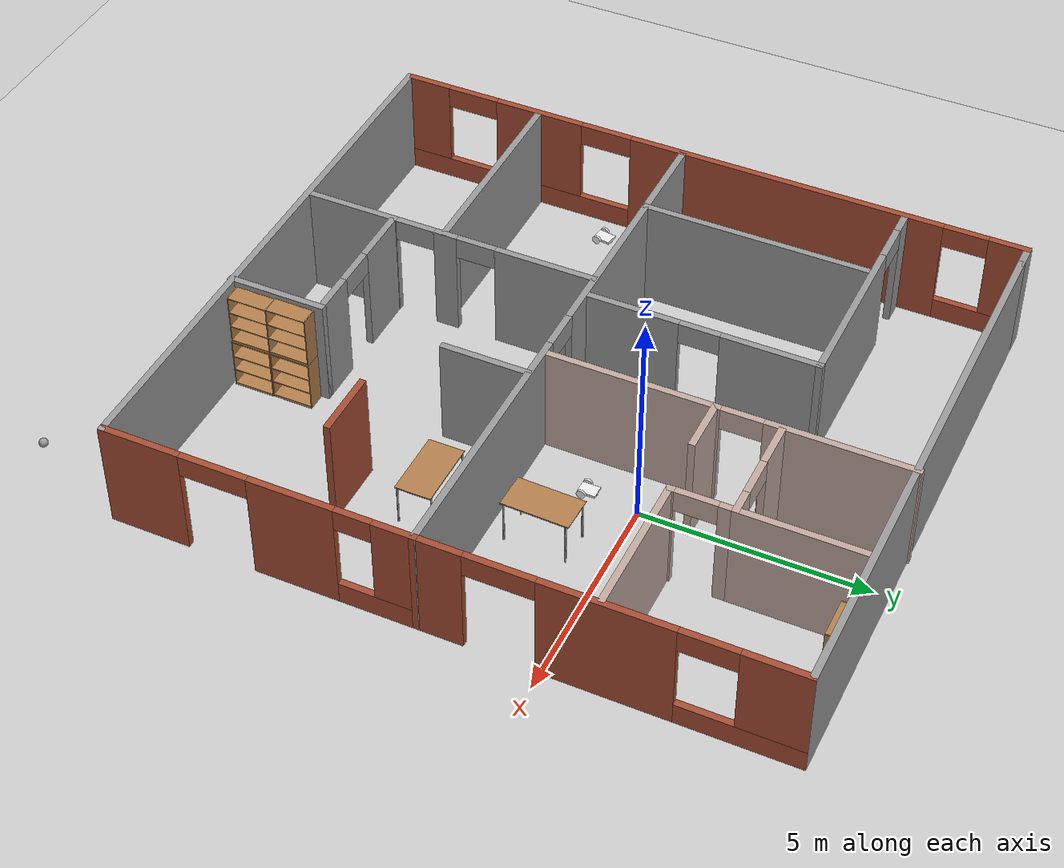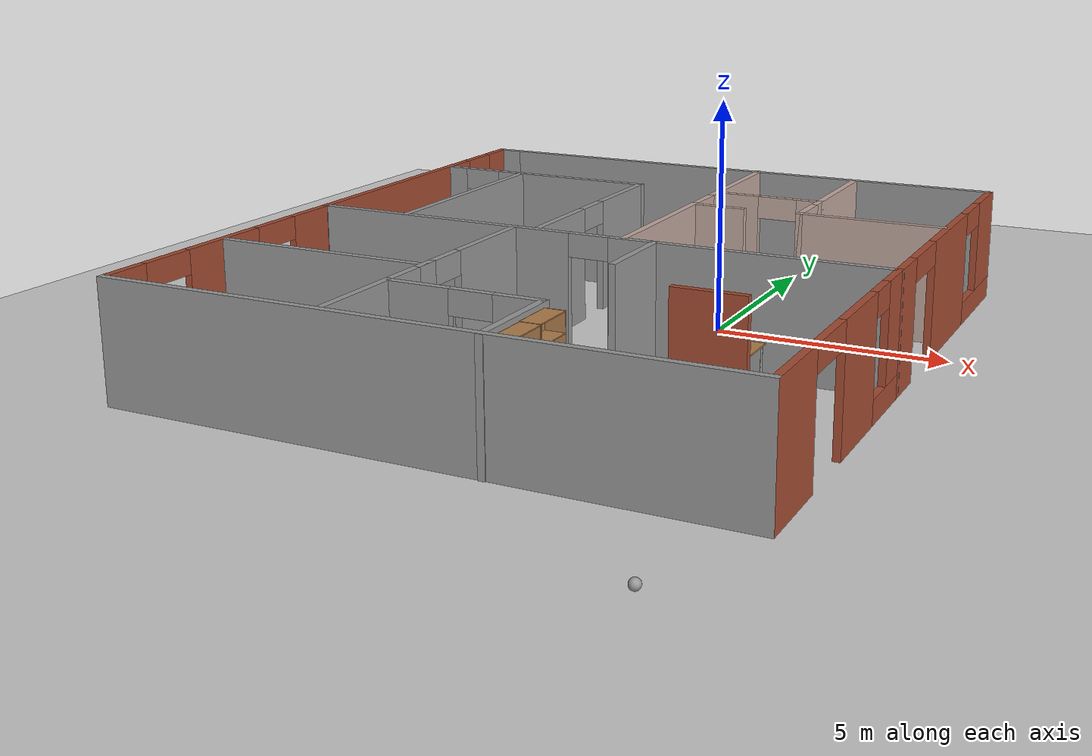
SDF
<sdf version="1.6">
 <world name="default">
  <plugin name="welcome_message" filename="libwelcome_message.so"/>
  <light name="sun" type="directional">
   <pose>0 0 10 0 -0 0</pose>
   <diffuse>0.8 0.8 0.8 1</diffuse>
   <specular>0.2 0.2 0.2 1</specular>
   <attenuation>
    <range>1000</range>
    <constant>0.9</constant>
    <linear>0.01</linear>
    <quadratic>0.001</quadratic>
   </attenuation>
   <direction>-0.5 0.1 -0.9</direction>
  </light>
  <model name="ground_plane">
   <static>1</static>
   <link name="link">
    <collision name="collision">
     <geometry><plane><normal>0 0 1</normal><size>100 100</size></plane></geometry>
     <surface>
      <contact><collide_bitmask>65535</collide_bitmask></contact>
      <friction><ode><mu>100</mu><mu2>50</mu2></ode></friction>
     </surface>
    </collision>
    <visual name="visual">
     <cast_shadows>0</cast_shadows>
     <geometry><plane><normal>0 0 1</normal><size>100 100</size></plane></geometry>
     <material>
      <script><uri>file://media/materials/scripts/gazebo.material</uri><name>Gazebo/Grey</name></script>
     </material>
    </visual>
   </link>
  </model>
  <gravity>0 0 -9.8</gravity>
  <magnetic_field>6e-06 2.3e-05 -4.2e-05</magnetic_field>
  <atmosphere type="adiabatic"/>
  <physics name="default_physics" default="0" type="ode">
   <max_step_size>0.001</max_step_size>
   <real_time_factor>1</real_time_factor>
   <real_time_update_rate>1000</real_time_update_rate>
  </physics>
  <scene><ambient>0.4 0.4 0.4 1</ambient><background>0.7 0.7 0.7 1</background><shadows>1</shadows></scene>
  <spherical_coordinates>
   <surface_model>EARTH_WGS84</surface_model>
   <latitude_deg>0</latitude_deg>
   <longitude_deg>0</longitude_deg>
   <elevation>0</elevation>
   <heading_deg>0</heading_deg>
  </spherical_coordinates>
  <model name="floor_plan">
   <pose>-1.88219 -2.06341 0 0 -0 0</pose>
   <link name="Wall_0">
    <pose>0 -0.539534 0 0 -0 3.14039</pose>
    <visual name="Wall_0_Visual_0">
     <pose>-3.50083 0 1.25 0 -0 0</pose>
     <geometry><box><size>5.99834 0.15 2.5</size></box></geometry>
     <material>
      <script><uri>file://media/materials/scripts/gazebo.material</uri><name>Gazebo/Grey</name></script>
      <ambient>1 1 1 1</ambient>
     </material>
     <meta><layer>0</layer></meta>
    </visual>
    <collision name="Wall_0_Collision_0">
     <geometry><box><size>5.99834 0.15 2.5</size></box></geometry>
     <pose>-3.50083 0 1.25 0 -0 0</pose>
    </collision>
    <visual name="Wall_0_Visual_1">
     <pose>3.44917 0 1.25 0 -0 0</pose>
     <geometry><box><size>6.10166 0.15 2.5</size></box></geometry>
     <material>
      <script><uri>file://media/materials/scripts/gazebo.material</uri><name>Gazebo/Grey</name></script>
      <ambient>1 1 1 1</ambient>
     </material>
     <meta><layer>0</layer></meta>
    </visual>
    <collision name="Wall_0_Collision_1">
     <geometry><box><size>6.10166 0.15 2.5</size></box></geometry>
     <pose>3.44917 0 1.25 0 -0 0</pose>
    </collision>
    <visual name="Wall_0_Visual_2">
     <pose>-0.051658 0 2.25 0 -0 0</pose>
     <geometry><box><size>0.9 0.15 0.5</size></box></geometry>
     <material>
      <script><uri>file://media/materials/scripts/gazebo.material</uri><name>Gazebo/Grey</name></script>
      <ambient>1 1 1 1</ambient>
     </material>
     <meta><layer>0</layer></meta>
    </visual>
    <collision name="Wall_0_Collision_2">
     <geometry><box><size>0.9 0.15 0.5</size></box></geometry>
     <pose>-0.051658 0 2.25 0 -0 0</pose>
    </collision>
   </link>
   <link name="Wall_11">
    <collision name="Wall_11_Collision">
     <geometry><box><size>2 0.15 2.5</size></box></geometry>
     <pose>0 0 1.25 0 -0 0</pose>
    </collision>
    <visual name="Wall_11_Visual">
     <pose>0 0 1.25 0 -0 0</pose>
     <geometry><box><size>2 0.15 2.5</size></box></geometry>
     <material>
      <script><uri>file://media/materials/scripts/gazebo.material</uri><name>Gazebo/Grey</name></script>
      <ambient>1 1 1 1</ambient>
     </material>
     <meta><layer>0</layer></meta>
    </visual>
    <pose>1.48948 -1.49915 0 0 0 -1.5708</pose>
   </link>
   <link name="Wall_13">
    <collision name="Wall_13_Collision">
     <geometry><box><size>1.5 0.15 2.5</size></box></geometry>
     <pose>0 0 1.25 0 -0 0</pose>
    </collision>
    <visual name="Wall_13_Visual">
     <pose>0 0 1.25 0 -0 0</pose>
     <geometry><box><size>1.5 0.15 2.5</size></box></geometry>
     <material>
      <script><uri>file://media/materials/scripts/gazebo.material</uri><name>Gazebo/Bricks</name></script>
      <ambient>1 1 1 1</ambient>
     </material>
     <meta><layer>0</layer></meta>
    </visual>
    <pose>3.82409 -3.40918 0 0 -0 0</pose>
   </link>
   <link name="Wall_15">
    <collision name="Wall_15_Collision">
     <geometry><box><size>4.75 0.15 2.5</size></box></geometry>
     <pose>0 0 1.25 0 -0 0</pose>
    </collision>
    <visual name="Wall_15_Visual">
     <pose>0 0 1.25 0 -0 0</pose>
     <geometry><box><size>4.75 0.15 2.5</size></box></geometry>
     <material>
      <script><uri>file://media/materials/scripts/gazebo.material</uri><name>Gazebo/Grey</name></script>
      <ambient>1 1 1 1</ambient>
     </material>
     <meta><layer>0</layer></meta>
    </visual>
    <pose>-3.97817 -4.0327 0 0 -0 3.14159</pose>
   </link>
   <link name="Wall_2">
    <pose>-6.42506 -3.93398 0 0 0 -1.5708</pose>
    <visual name="Wall_2_Visual_0">
     <pose>-2.80871 0 1.25 0 -0 0</pose>
     <geometry><box><size>1.30653 0.15 2.5</size></box></geometry>
     <material>
      <script><uri>file://media/materials/scripts/gazebo.material</uri><name>Gazebo/Bricks</name></script>
      <ambient>1 1 1 1</ambient>
     </material>
     <meta><layer>0</layer></meta>
    </visual>
    <collision name="Wall_2_Collision_0">
     <geometry><box><size>1.30653 0.15 2.5</size></box></geometry>
     <pose>-2.80871 0 1.25 0 -0 0</pose>
    </collision>
    <visual name="Wall_2_Visual_1">
     <pose>0.653263 0 0.25 0 -0 0</pose>
     <geometry><box><size>5.61743 0.15 0.5</size></box></geometry>
     <material>
      <script><uri>file://media/materials/scripts/gazebo.material</uri><name>Gazebo/Bricks</name></script>
      <ambient>1 1 1 1</ambient>
     </material>
     <meta><layer>0</layer></meta>
    </visual>
    <collision name="Wall_2_Collision_1">
     <geometry><box><size>5.61743 0.15 0.5</size></box></geometry>
     <pose>0.653263 0 0.25 0 -0 0</pose>
    </collision>
    <visual name="Wall_2_Visual_2">
     <pose>0.095441 0 1.5 0 -0 0</pose>
     <geometry><box><size>2.10179 0.15 2</size></box></geometry>
     <material>
      <script><uri>file://media/materials/scripts/gazebo.material</uri><name>Gazebo/Bricks</name></script>
      <ambient>1 1 1 1</ambient>
     </material>
     <meta><layer>0</layer></meta>
    </visual>
    <collision name="Wall_2_Collision_2">
     <geometry><box><size>2.10179 0.15 2</size></box></geometry>
     <pose>0.095441 0 1.5 0 -0 0</pose>
    </collision>
    <visual name="Wall_2_Visual_3">
     <pose>2.90416 0 1.5 0 -0 0</pose>
     <geometry><box><size>1.11564 0.15 2</size></box></geometry>
     <material>
      <script><uri>file://media/materials/scripts/gazebo.material</uri><name>Gazebo/Bricks</name></script>
      <ambient>1 1 1 1</ambient>
     </material>
     <meta><layer>0</layer></meta>
    </visual>
    <collision name="Wall_2_Collision_3">
     <geometry><box><size>1.11564 0.15 2</size></box></geometry>
     <pose>2.90416 0 1.5 0 -0 0</pose>
    </collision>
    <visual name="Wall_2_Visual_4">
     <pose>-1.55545 0 2.25 0 -0 0</pose>
     <geometry><box><size>1.2 0.15 0.5</size></box></geometry>
     <material>
      <script><uri>file://media/materials/scripts/gazebo.material</uri><name>Gazebo/Bricks</name></script>
      <ambient>1 1 1 1</ambient>
     </material>
     <meta><layer>0</layer></meta>
    </visual>
    <collision name="Wall_2_Collision_4">
     <geometry><box><size>1.2 0.15 0.5</size></box></geometry>
     <pose>-1.55545 0 2.25 0 -0 0</pose>
    </collision>
    <visual name="Wall_2_Visual_5">
     <pose>1.74633 0 2.25 0 -0 0</pose>
     <geometry><box><size>1.2 0.15 0.5</size></box></geometry>
     <material>
      <script><uri>file://media/materials/scripts/gazebo.material</uri><name>Gazebo/Bricks</name></script>
      <ambient>1 1 1 1</ambient>
     </material>
     <meta><layer>0</layer></meta>
    </visual>
    <collision name="Wall_2_Collision_5">
     <geometry><box><size>1.2 0.15 0.5</size></box></geometry>
     <pose>1.74633 0 2.25 0 -0 0</pose>
    </collision>
   </link>
   <link name="Wall_3">
    <collision name="Wall_3_Collision">
     <geometry><box><size>13 0.15 2.5</size></box></geometry>
     <pose>0 0 1.25 0 -0 0</pose>
    </collision>
    <visual name="Wall_3_Visual">
     <pose>0 0 1.25 0 -0 0</pose>
     <geometry><box><size>13 0.15 2.5</size></box></geometry>
     <material>
      <script><uri>file://media/materials/scripts/gazebo.material</uri><name>Gazebo/Grey</name></script>
      <ambient>1 1 1 1</ambient>
     </material>
     <meta><layer>0</layer></meta>
    </visual>
    <pose>0 -7.32112 0 0 0 -2.4e-05</pose>
   </link>
   <link name="Wall_36">
    <pose>-1.17934 2.06051 0 0 -0 1.5708</pose>
    <visual name="Wall_36_Visual_0">
     <pose>-1.55306 0 1.25 0 -0 0</pose>
     <geometry><box><size>2.14389 0.15 2.5</size></box></geometry>
     <material>
      <script><uri>file://media/materials/scripts/gazebo.material</uri><name>Gazebo/Grey</name></script>
      <ambient>1 1 1 1</ambient>
     </material>
     <meta><layer>0</layer></meta>
    </visual>
    <collision name="Wall_36_Collision_0">
     <geometry><box><size>2.14389 0.15 2.5</size></box></geometry>
     <pose>-1.55306 0 1.25 0 -0 0</pose>
    </collision>
    <visual name="Wall_36_Visual_1">
     <pose>1.52195 0 1.25 0 -0 0</pose>
     <geometry><box><size>2.20611 0.15 2.5</size></box></geometry>
     <material>
      <script><uri>file://media/materials/scripts/gazebo.material</uri><name>Gazebo/Grey</name></script>
      <ambient>1 1 1 1</ambient>
     </material>
     <meta><layer>0</layer></meta>
    </visual>
    <collision name="Wall_36_Collision_1">
     <geometry><box><size>2.20611 0.15 2.5</size></box></geometry>
     <pose>1.52195 0 1.25 0 -0 0</pose>
    </collision>
    <visual name="Wall_36_Visual_2">
     <pose>-0.031111 0 2.25 0 -0 0</pose>
     <geometry><box><size>0.9 0.15 0.5</size></box></geometry>
     <material>
      <script><uri>file://media/materials/scripts/gazebo.material</uri><name>Gazebo/Grey</name></script>
      <ambient>1 1 1 1</ambient>
     </material>
     <meta><layer>0</layer></meta>
    </visual>
    <collision name="Wall_36_Collision_2">
     <geometry><box><size>0.9 0.15 0.5</size></box></geometry>
     <pose>-0.031111 0 2.25 0 -0 0</pose>
    </collision>
   </link>
   <link name="Wall_37">
    <pose>-3.72933 4.61051 0 0 -0 3.14159</pose>
    <visual name="Wall_37_Visual_0">
     <pose>-0.694741 0 1.25 0 -0 0</pose>
     <geometry><box><size>3.86052 0.15 2.5</size></box></geometry>
     <material>
      <script><uri>file://media/materials/scripts/gazebo.material</uri><name>Gazebo/Grey</name></script>
      <ambient>1 1 1 1</ambient>
     </material>
     <meta><layer>0</layer></meta>
    </visual>
    <collision name="Wall_37_Collision_0">
     <geometry><box><size>3.86052 0.15 2.5</size></box></geometry>
     <pose>-0.694741 0 1.25 0 -0 0</pose>
    </collision>
    <visual name="Wall_37_Visual_1">
     <pose>2.38026 0 1.25 0 -0 0</pose>
     <geometry><box><size>0.489482 0.15 2.5</size></box></geometry>
     <material>
      <script><uri>file://media/materials/scripts/gazebo.material</uri><name>Gazebo/Grey</name></script>
      <ambient>1 1 1 1</ambient>
     </material>
     <meta><layer>0</layer></meta>
    </visual>
    <collision name="Wall_37_Collision_1">
     <geometry><box><size>0.489482 0.15 2.5</size></box></geometry>
     <pose>2.38026 0 1.25 0 -0 0</pose>
    </collision>
    <visual name="Wall_37_Visual_2">
     <pose>1.68552 0 2.25 0 -0 0</pose>
     <geometry><box><size>0.9 0.15 0.5</size></box></geometry>
     <material>
      <script><uri>file://media/materials/scripts/gazebo.material</uri><name>Gazebo/Grey</name></script>
      <ambient>1 1 1 1</ambient>
     </material>
     <meta><layer>0</layer></meta>
    </visual>
    <collision name="Wall_37_Collision_2">
     <geometry><box><size>0.9 0.15 0.5</size></box></geometry>
     <pose>1.68552 0 2.25 0 -0 0</pose>
    </collision>
   </link>
   <link name="Wall_39">
    <collision name="Wall_39_Collision">
     <geometry><box><size>5.25 0.15 2.5</size></box></geometry>
     <pose>0 0 1.25 0 -0 0</pose>
    </collision>
    <visual name="Wall_39_Visual">
     <pose>0 0 1.25 0 -0 0</pose>
     <geometry><box><size>5.25 0.15 2.5</size></box></geometry>
     <material>
      <script><uri>file://media/materials/scripts/gazebo.material</uri><name>Gazebo/Grey</name></script>
      <ambient>1 1 1 1</ambient>
     </material>
     <meta><layer>0</layer></meta>
    </visual>
    <pose>-4.34796 2.03294 0 0 0 -1.5708</pose>
   </link>
   <link name="Wall_4">
    <pose>6.42506 -3.93427 0 0 -0 1.5708</pose>
    <visual name="Wall_4_Visual_0">
     <pose>-2.56147 0 1.25 0 -0 0</pose>
     <geometry><box><size>1.80105 0.15 2.5</size></box></geometry>
     <material>
      <script><uri>file://media/materials/scripts/gazebo.material</uri><name>Gazebo/Bricks</name></script>
      <ambient>1 1 1 1</ambient>
     </material>
     <meta><layer>0</layer></meta>
    </visual>
    <collision name="Wall_4_Collision_0">
     <geometry><box><size>1.80105 0.15 2.5</size></box></geometry>
     <pose>-2.56147 0 1.25 0 -0 0</pose>
    </collision>
    <visual name="Wall_4_Visual_1">
     <pose>0.775723 0 1.25 0 -0 0</pose>
     <geometry><box><size>1.87334 0.15 2.5</size></box></geometry>
     <material>
      <script><uri>file://media/materials/scripts/gazebo.material</uri><name>Gazebo/Bricks</name></script>
      <ambient>1 1 1 1</ambient>
     </material>
     <meta><layer>0</layer></meta>
    </visual>
    <collision name="Wall_4_Collision_1">
     <geometry><box><size>1.87334 0.15 2.5</size></box></geometry>
     <pose>0.775723 0 1.25 0 -0 0</pose>
    </collision>
    <visual name="Wall_4_Visual_2">
     <pose>2.5872 0 0.25 0 -0 0</pose>
     <geometry><box><size>1.74961 0.15 0.5</size></box></geometry>
     <material>
      <script><uri>file://media/materials/scripts/gazebo.material</uri><name>Gazebo/Bricks</name></script>
      <ambient>1 1 1 1</ambient>
     </material>
     <meta><layer>0</layer></meta>
    </visual>
    <collision name="Wall_4_Collision_2">
     <geometry><box><size>1.74961 0.15 0.5</size></box></geometry>
     <pose>2.5872 0 0.25 0 -0 0</pose>
    </collision>
    <visual name="Wall_4_Visual_3">
     <pose>2.9872 0 1.5 0 -0 0</pose>
     <geometry><box><size>0.949605 0.15 2</size></box></geometry>
     <material>
      <script><uri>file://media/materials/scripts/gazebo.material</uri><name>Gazebo/Bricks</name></script>
      <ambient>1 1 1 1</ambient>
     </material>
     <meta><layer>0</layer></meta>
    </visual>
    <collision name="Wall_4_Collision_3">
     <geometry><box><size>0.949605 0.15 2</size></box></geometry>
     <pose>2.9872 0 1.5 0 -0 0</pose>
    </collision>
    <visual name="Wall_4_Visual_4">
     <pose>-0.910948 0 2.25 0 -0 0</pose>
     <geometry><box><size>1.5 0.15 0.5</size></box></geometry>
     <material>
      <script><uri>file://media/materials/scripts/gazebo.material</uri><name>Gazebo/Bricks</name></script>
      <ambient>1 1 1 1</ambient>
     </material>
     <meta><layer>0</layer></meta>
    </visual>
    <collision name="Wall_4_Collision_4">
     <geometry><box><size>1.5 0.15 0.5</size></box></geometry>
     <pose>-0.910948 0 2.25 0 -0 0</pose>
    </collision>
    <visual name="Wall_4_Visual_5">
     <pose>2.11239 0 2.25 0 -0 0</pose>
     <geometry><box><size>0.8 0.15 0.5</size></box></geometry>
     <material>
      <script><uri>file://media/materials/scripts/gazebo.material</uri><name>Gazebo/Bricks</name></script>
      <ambient>1 1 1 1</ambient>
     </material>
     <meta><layer>0</layer></meta>
    </visual>
    <collision name="Wall_4_Collision_5">
     <geometry><box><size>0.8 0.15 0.5</size></box></geometry>
     <pose>2.11239 0 2.25 0 -0 0</pose>
    </collision>
   </link>
   <link name="Wall_45">
    <pose>6.425 3.37786 0 0 -0 1.57081</pose>
    <visual name="Wall_45_Visual_0">
     <pose>-3.45923 0 1.25 0 -0 0</pose>
     <geometry><box><size>1.08155 0.15 2.5</size></box></geometry>
     <material>
      <script><uri>file://media/materials/scripts/gazebo.material</uri><name>Gazebo/Bricks</name></script>
      <ambient>1 1 1 1</ambient>
     </material>
     <meta><layer>0</layer></meta>
    </visual>
    <collision name="Wall_45_Collision_0">
     <geometry><box><size>1.08155 0.15 2.5</size></box></geometry>
     <pose>-3.45923 0 1.25 0 -0 0</pose>
    </collision>
    <visual name="Wall_45_Visual_1">
     <pose>-0.023066 0 1.25 0 -0 0</pose>
     <geometry><box><size>2.79077 0.15 2.5</size></box></geometry>
     <material>
      <script><uri>file://media/materials/scripts/gazebo.material</uri><name>Gazebo/Bricks</name></script>
      <ambient>1 1 1 1</ambient>
     </material>
     <meta><layer>0</layer></meta>
    </visual>
    <collision name="Wall_45_Collision_1">
     <geometry><box><size>2.79077 0.15 2.5</size></box></geometry>
     <pose>-0.023066 0 1.25 0 -0 0</pose>
    </collision>
    <visual name="Wall_45_Visual_2">
     <pose>2.68616 0 0.25 0 -0 0</pose>
     <geometry><box><size>2.62768 0.15 0.5</size></box></geometry>
     <material>
      <script><uri>file://media/materials/scripts/gazebo.material</uri><name>Gazebo/Bricks</name></script>
      <ambient>1 1 1 1</ambient>
     </material>
     <meta><layer>0</layer></meta>
    </visual>
    <collision name="Wall_45_Collision_2">
     <geometry><box><size>2.62768 0.15 0.5</size></box></geometry>
     <pose>2.68616 0 0.25 0 -0 0</pose>
    </collision>
    <visual name="Wall_45_Visual_3">
     <pose>3.28616 0 1.5 0 -0 0</pose>
     <geometry><box><size>1.42768 0.15 2</size></box></geometry>
     <material>
      <script><uri>file://media/materials/scripts/gazebo.material</uri><name>Gazebo/Bricks</name></script>
      <ambient>1 1 1 1</ambient>
     </material>
     <meta><layer>0</layer></meta>
    </visual>
    <collision name="Wall_45_Collision_3">
     <geometry><box><size>1.42768 0.15 2</size></box></geometry>
     <pose>3.28616 0 1.5 0 -0 0</pose>
    </collision>
    <visual name="Wall_45_Visual_4">
     <pose>-2.16845 0 2.25 0 -0 0</pose>
     <geometry><box><size>1.5 0.15 0.5</size></box></geometry>
     <material>
      <script><uri>file://media/materials/scripts/gazebo.material</uri><name>Gazebo/Bricks</name></script>
      <ambient>1 1 1 1</ambient>
     </material>
     <meta><layer>0</layer></meta>
    </visual>
    <collision name="Wall_45_Collision_4">
     <geometry><box><size>1.5 0.15 0.5</size></box></geometry>
     <pose>-2.16845 0 2.25 0 -0 0</pose>
    </collision>
    <visual name="Wall_45_Visual_5">
     <pose>1.97232 0 2.25 0 -0 0</pose>
     <geometry><box><size>1.2 0.15 0.5</size></box></geometry>
     <material>
      <script><uri>file://media/materials/scripts/gazebo.material</uri><name>Gazebo/Bricks</name></script>
      <ambient>1 1 1 1</ambient>
     </material>
     <meta><layer>0</layer></meta>
    </visual>
    <collision name="Wall_45_Collision_5">
     <geometry><box><size>1.2 0.15 0.5</size></box></geometry>
     <pose>1.97232 0 2.25 0 -0 0</pose>
    </collision>
   </link>
   <link name="Wall_46">
    <collision name="Wall_46_Collision">
     <geometry><box><size>12.5 0.15 2.5</size></box></geometry>
     <pose>0 0 1.25 0 -0 0</pose>
    </collision>
    <visual name="Wall_46_Visual">
     <pose>0 0 1.25 0 -0 0</pose>
     <geometry><box><size>12.5 0.15 2.5</size></box></geometry>
     <material>
      <script><uri>file://media/materials/scripts/gazebo.material</uri><name>Gazebo/Grey</name></script>
      <ambient>1 1 1 1</ambient>
     </material>
     <meta><layer>0</layer></meta>
    </visual>
    <pose>0.249944 7.303 0 0 -0 3.14159</pose>
   </link>
   <link name="Wall_48">
    <pose>-6.42506 3.378 0 0 -0 1.5708</pose>
    <visual name="Wall_48_Visual_0">
     <pose>-0.956686 0 1.25 0 -0 0</pose>
     <geometry><box><size>6.08663 0.15 2.5</size></box></geometry>
     <material>
      <script><uri>file://media/materials/scripts/gazebo.material</uri><name>Gazebo/Bricks</name></script>
      <ambient>1 1 1 1</ambient>
     </material>
     <meta><layer>0</layer></meta>
    </visual>
    <collision name="Wall_48_Collision_0">
     <geometry><box><size>6.08663 0.15 2.5</size></box></geometry>
     <pose>-0.956686 0 1.25 0 -0 0</pose>
    </collision>
    <visual name="Wall_48_Visual_1">
     <pose>3.04331 0 0.25 0 -0 0</pose>
     <geometry><box><size>1.91337 0.15 0.5</size></box></geometry>
     <material>
      <script><uri>file://media/materials/scripts/gazebo.material</uri><name>Gazebo/Bricks</name></script>
      <ambient>1 1 1 1</ambient>
     </material>
     <meta><layer>0</layer></meta>
    </visual>
    <collision name="Wall_48_Collision_1">
     <geometry><box><size>1.91337 0.15 0.5</size></box></geometry>
     <pose>3.04331 0 0.25 0 -0 0</pose>
    </collision>
    <visual name="Wall_48_Visual_2">
     <pose>3.54331 0 1.5 0 -0 0</pose>
     <geometry><box><size>0.913372 0.15 2</size></box></geometry>
     <material>
      <script><uri>file://media/materials/scripts/gazebo.material</uri><name>Gazebo/Bricks</name></script>
      <ambient>1 1 1 1</ambient>
     </material>
     <meta><layer>0</layer></meta>
    </visual>
    <collision name="Wall_48_Collision_2">
     <geometry><box><size>0.913372 0.15 2</size></box></geometry>
     <pose>3.54331 0 1.5 0 -0 0</pose>
    </collision>
    <visual name="Wall_48_Visual_3">
     <pose>2.58663 0 2.25 0 -0 0</pose>
     <geometry><box><size>1 0.15 0.5</size></box></geometry>
     <material>
      <script><uri>file://media/materials/scripts/gazebo.material</uri><name>Gazebo/Bricks</name></script>
      <ambient>1 1 1 1</ambient>
     </material>
     <meta><layer>0</layer></meta>
    </visual>
    <collision name="Wall_48_Collision_3">
     <geometry><box><size>1 0.15 0.5</size></box></geometry>
     <pose>2.58663 0 2.25 0 -0 0</pose>
    </collision>
   </link>
   <link name="Wall_49">
    <collision name="Wall_49_Collision">
     <geometry><box><size>0.65 0.15 2.5</size></box></geometry>
     <pose>0 0 1.25 0 -0 0</pose>
    </collision>
    <visual name="Wall_49_Visual">
     <pose>0 0 1.25 0 -0 0</pose>
     <geometry><box><size>0.65 0.15 2.5</size></box></geometry>
     <material>
      <script><uri>file://media/materials/scripts/gazebo.material</uri><name>Gazebo/Grey</name></script>
      <ambient>1 1 1 1</ambient>
     </material>
     <meta><layer>0</layer></meta>
    </visual>
    <pose>-6.17506 7.303 0 0 -0 0</pose>
   </link>
   <link name="Wall_51">
    <pose>0.800151 3.41451 0 0 -0 1.5708</pose>
    <visual name="Wall_51_Visual_0">
     <pose>-2.06358 0 1.25 0 -0 0</pose>
     <geometry><box><size>3.87284 0.15 2.5</size></box></geometry>
     <material>
      <script><uri>file://media/materials/scripts/gazebo.material</uri><name>Gazebo/Grey</name></script>
      <ambient>0.760784 0.662745 0.627451 1</ambient>
     </material>
     <meta><layer>0</layer></meta>
    </visual>
    <collision name="Wall_51_Collision_0">
     <geometry><box><size>3.87284 0.15 2.5</size></box></geometry>
     <pose>-2.06358 0 1.25 0 -0 0</pose>
    </collision>
    <visual name="Wall_51_Visual_1">
     <pose>2.38642 0 1.25 0 -0 0</pose>
     <geometry><box><size>3.22716 0.15 2.5</size></box></geometry>
     <material>
      <script><uri>file://media/materials/scripts/gazebo.material</uri><name>Gazebo/Grey</name></script>
      <ambient>0.760784 0.662745 0.627451 1</ambient>
     </material>
     <meta><layer>0</layer></meta>
    </visual>
    <collision name="Wall_51_Collision_1">
     <geometry><box><size>3.22716 0.15 2.5</size></box></geometry>
     <pose>2.38642 0 1.25 0 -0 0</pose>
    </collision>
    <visual name="Wall_51_Visual_2">
     <pose>0.322836 0 2.25 0 -0 0</pose>
     <geometry><box><size>0.9 0.15 0.5</size></box></geometry>
     <material>
      <script><uri>file://media/materials/scripts/gazebo.material</uri><name>Gazebo/Grey</name></script>
      <ambient>0.760784 0.662745 0.627451 1</ambient>
     </material>
     <meta><layer>0</layer></meta>
    </visual>
    <collision name="Wall_51_Collision_2">
     <geometry><box><size>0.9 0.15 0.5</size></box></geometry>
     <pose>0.322836 0 2.25 0 -0 0</pose>
    </collision>
   </link>
   <link name="Wall_53">
    <pose>2.06768 4.57778 0 0 -0 0</pose>
    <visual name="Wall_53_Visual_0">
     <pose>-0.747106 0 1.25 0 -0 0</pose>
     <geometry><box><size>1.00579 0.15 2.5</size></box></geometry>
     <material>
      <script><uri>file://media/materials/scripts/gazebo.material</uri><name>Gazebo/Grey</name></script>
      <ambient>0.760784 0.662745 0.627451 1</ambient>
     </material>
     <meta><layer>0</layer></meta>
    </visual>
    <collision name="Wall_53_Collision_0">
     <geometry><box><size>1.00579 0.15 2.5</size></box></geometry>
     <pose>-0.747106 0 1.25 0 -0 0</pose>
    </collision>
    <visual name="Wall_53_Visual_1">
     <pose>0.952894 0 1.25 0 -0 0</pose>
     <geometry><box><size>0.594213 0.15 2.5</size></box></geometry>
     <material>
      <script><uri>file://media/materials/scripts/gazebo.material</uri><name>Gazebo/Grey</name></script>
      <ambient>0.760784 0.662745 0.627451 1</ambient>
     </material>
     <meta><layer>0</layer></meta>
    </visual>
    <collision name="Wall_53_Collision_1">
     <geometry><box><size>0.594213 0.15 2.5</size></box></geometry>
     <pose>0.952894 0 1.25 0 -0 0</pose>
    </collision>
    <visual name="Wall_53_Visual_2">
     <pose>0.205787 0 2.25 0 -0 0</pose>
     <geometry><box><size>0.9 0.15 0.5</size></box></geometry>
     <material>
      <script><uri>file://media/materials/scripts/gazebo.material</uri><name>Gazebo/Grey</name></script>
      <ambient>0.760784 0.662745 0.627451 1</ambient>
     </material>
     <meta><layer>0</layer></meta>
    </visual>
    <collision name="Wall_53_Collision_2">
     <geometry><box><size>0.9 0.15 0.5</size></box></geometry>
     <pose>0.205787 0 2.25 0 -0 0</pose>
    </collision>
   </link>
   <link name="Wall_54">
    <collision name="Wall_54_Collision">
     <geometry><box><size>2.75 0.15 2.5</size></box></geometry>
     <pose>0 0 1.25 0 -0 0</pose>
    </collision>
    <visual name="Wall_54_Visual">
     <pose>0 0 1.25 0 -0 0</pose>
     <geometry><box><size>2.75 0.15 2.5</size></box></geometry>
     <material>
      <script><uri>file://media/materials/scripts/gazebo.material</uri><name>Gazebo/Grey</name></script>
      <ambient>0.760784 0.662745 0.627451 1</ambient>
     </material>
     <meta><layer>0</layer></meta>
    </visual>
    <pose>3.24268 5.87778 0 0 -0 1.5708</pose>
   </link>
   <link name="Wall_56">
    <pose>3.24268 3.90278 0 0 0 -1.5708</pose>
    <visual name="Wall_56_Visual_0">
     <pose>-0.543058 0 1.25 0 -0 0</pose>
     <geometry><box><size>0.413884 0.15 2.5</size></box></geometry>
     <material>
      <script><uri>file://media/materials/scripts/gazebo.material</uri><name>Gazebo/Grey</name></script>
      <ambient>0.760784 0.662745 0.627451 1</ambient>
     </material>
     <meta><layer>0</layer></meta>
    </visual>
    <collision name="Wall_56_Collision_0">
     <geometry><box><size>0.413884 0.15 2.5</size></box></geometry>
     <pose>-0.543058 0 1.25 0 -0 0</pose>
    </collision>
    <visual name="Wall_56_Visual_1">
     <pose>0.656942 0 1.25 0 -0 0</pose>
     <geometry><box><size>0.186116 0.15 2.5</size></box></geometry>
     <material>
      <script><uri>file://media/materials/scripts/gazebo.material</uri><name>Gazebo/Grey</name></script>
      <ambient>0.760784 0.662745 0.627451 1</ambient>
     </material>
     <meta><layer>0</layer></meta>
    </visual>
    <collision name="Wall_56_Collision_1">
     <geometry><box><size>0.186116 0.15 2.5</size></box></geometry>
     <pose>0.656942 0 1.25 0 -0 0</pose>
    </collision>
    <visual name="Wall_56_Visual_2">
     <pose>0.113884 0 2.25 0 -0 0</pose>
     <geometry><box><size>0.9 0.15 0.5</size></box></geometry>
     <material>
      <script><uri>file://media/materials/scripts/gazebo.material</uri><name>Gazebo/Grey</name></script>
      <ambient>0.760784 0.662745 0.627451 1</ambient>
     </material>
     <meta><layer>0</layer></meta>
    </visual>
    <collision name="Wall_56_Collision_2">
     <geometry><box><size>0.9 0.15 0.5</size></box></geometry>
     <pose>0.113884 0 2.25 0 -0 0</pose>
    </collision>
   </link>
   <link name="Wall_57">
    <collision name="Wall_57_Collision">
     <geometry><box><size>3.25 0.15 2.5</size></box></geometry>
     <pose>0 0 1.25 0 -0 0</pose>
    </collision>
    <visual name="Wall_57_Visual">
     <pose>0 0 1.25 0 -0 0</pose>
     <geometry><box><size>3.25 0.15 2.5</size></box></geometry>
     <material>
      <script><uri>file://media/materials/scripts/gazebo.material</uri><name>Gazebo/Grey</name></script>
      <ambient>0.760784 0.662745 0.627451 1</ambient>
     </material>
     <meta><layer>0</layer></meta>
    </visual>
    <pose>4.79268 3.22778 0 0 -0 0</pose>
   </link>
   <link name="Wall_59">
    <collision name="Wall_59_Collision">
     <geometry><box><size>1.25 0.15 2.5</size></box></geometry>
     <pose>0 0 1.25 0 -0 0</pose>
    </collision>
    <visual name="Wall_59_Visual">
     <pose>0 0 1.25 0 -0 0</pose>
     <geometry><box><size>1.25 0.15 2.5</size></box></geometry>
     <material>
      <script><uri>file://media/materials/scripts/gazebo.material</uri><name>Gazebo/Grey</name></script>
      <ambient>0.760784 0.662745 0.627451 1</ambient>
     </material>
     <meta><layer>0</layer></meta>
    </visual>
    <pose>1.382 3.16183 0 0 -0 0</pose>
   </link>
   <link name="Wall_6">
    <pose>-1.67816 -3.87415 0 0 0 -1.5708</pose>
    <visual name="Wall_6_Visual_0">
     <pose>-2.21563 0 1.25 0 -0 0</pose>
     <geometry><box><size>2.31875 0.15 2.5</size></box></geometry>
     <material>
      <script><uri>file://media/materials/scripts/gazebo.material</uri><name>Gazebo/Grey</name></script>
      <ambient>1 1 1 1</ambient>
     </material>
     <meta><layer>0</layer></meta>
    </visual>
    <collision name="Wall_6_Collision_0">
     <geometry><box><size>2.31875 0.15 2.5</size></box></geometry>
     <pose>-2.21563 0 1.25 0 -0 0</pose>
    </collision>
    <visual name="Wall_6_Visual_1">
     <pose>0.110792 0 1.25 0 -0 0</pose>
     <geometry><box><size>0.534083 0.15 2.5</size></box></geometry>
     <material>
      <script><uri>file://media/materials/scripts/gazebo.material</uri><name>Gazebo/Grey</name></script>
      <ambient>1 1 1 1</ambient>
     </material>
     <meta><layer>0</layer></meta>
    </visual>
    <collision name="Wall_6_Collision_1">
     <geometry><box><size>0.534083 0.15 2.5</size></box></geometry>
     <pose>0.110792 0 1.25 0 -0 0</pose>
    </collision>
    <visual name="Wall_6_Visual_2">
     <pose>2.32642 0 1.25 0 -0 0</pose>
     <geometry><box><size>2.09717 0.15 2.5</size></box></geometry>
     <material>
      <script><uri>file://media/materials/scripts/gazebo.material</uri><name>Gazebo/Grey</name></script>
      <ambient>1 1 1 1</ambient>
     </material>
     <meta><layer>0</layer></meta>
    </visual>
    <collision name="Wall_6_Collision_2">
     <geometry><box><size>2.09717 0.15 2.5</size></box></geometry>
     <pose>2.32642 0 1.25 0 -0 0</pose>
    </collision>
    <visual name="Wall_6_Visual_3">
     <pose>-0.60625 0 2.25 0 -0 0</pose>
     <geometry><box><size>0.9 0.15 0.5</size></box></geometry>
     <material>
      <script><uri>file://media/materials/scripts/gazebo.material</uri><name>Gazebo/Grey</name></script>
      <ambient>1 1 1 1</ambient>
     </material>
     <meta><layer>0</layer></meta>
    </visual>
    <collision name="Wall_6_Collision_3">
     <geometry><box><size>0.9 0.15 0.5</size></box></geometry>
     <pose>-0.60625 0 2.25 0 -0 0</pose>
    </collision>
    <visual name="Wall_6_Visual_4">
     <pose>0.827833 0 2.25 0 -0 0</pose>
     <geometry><box><size>0.9 0.15 0.5</size></box></geometry>
     <material>
      <script><uri>file://media/materials/scripts/gazebo.material</uri><name>Gazebo/Grey</name></script>
      <ambient>1 1 1 1</ambient>
     </material>
     <meta><layer>0</layer></meta>
    </visual>
    <collision name="Wall_6_Collision_4">
     <geometry><box><size>0.9 0.15 0.5</size></box></geometry>
     <pose>0.827833 0 2.25 0 -0 0</pose>
    </collision>
   </link>
   <link name="Wall_8">
    <pose>-0.047711 -5.23951 0 0 -0 0</pose>
    <visual name="Wall_8_Visual_0">
     <pose>-0.96773 0 1.25 0 -0 0</pose>
     <geometry><box><size>1.31454 0.15 2.5</size></box></geometry>
     <material>
      <script><uri>file://media/materials/scripts/gazebo.material</uri><name>Gazebo/Grey</name></script>
      <ambient>1 1 1 1</ambient>
     </material>
     <meta><layer>0</layer></meta>
    </visual>
    <collision name="Wall_8_Collision_0">
     <geometry><box><size>1.31454 0.15 2.5</size></box></geometry>
     <pose>-0.96773 0 1.25 0 -0 0</pose>
    </collision>
    <visual name="Wall_8_Visual_1">
     <pose>1.10727 0 1.25 0 -0 0</pose>
     <geometry><box><size>1.03546 0.15 2.5</size></box></geometry>
     <material>
      <script><uri>file://media/materials/scripts/gazebo.material</uri><name>Gazebo/Grey</name></script>
      <ambient>1 1 1 1</ambient>
     </material>
     <meta><layer>0</layer></meta>
    </visual>
    <collision name="Wall_8_Collision_1">
     <geometry><box><size>1.03546 0.15 2.5</size></box></geometry>
     <pose>1.10727 0 1.25 0 -0 0</pose>
    </collision>
    <visual name="Wall_8_Visual_2">
     <pose>0.13954 0 2.25 0 -0 0</pose>
     <geometry><box><size>0.9 0.15 0.5</size></box></geometry>
     <material>
      <script><uri>file://media/materials/scripts/gazebo.material</uri><name>Gazebo/Grey</name></script>
      <ambient>1 1 1 1</ambient>
     </material>
     <meta><layer>0</layer></meta>
    </visual>
    <collision name="Wall_8_Collision_2">
     <geometry><box><size>0.9 0.15 0.5</size></box></geometry>
     <pose>0.13954 0 2.25 0 -0 0</pose>
    </collision>
   </link>
   <link name="Wall_9">
    <collision name="Wall_9_Collision">
     <geometry><box><size>2.25 0.15 2.5</size></box></geometry>
     <pose>0 0 1.25 0 -0 0</pose>
    </collision>
    <visual name="Wall_9_Visual">
     <pose>0 0 1.25 0 -0 0</pose>
     <geometry><box><size>2.25 0.15 2.5</size></box></geometry>
     <material>
      <script><uri>file://media/materials/scripts/gazebo.material</uri><name>Gazebo/Grey</name></script>
      <ambient>1 1 1 1</ambient>
     </material>
     <meta><layer>0</layer></meta>
    </visual>
    <pose>1.50229 -6.28951 0 0 0 -1.5708</pose>
   </link>
   <static>1</static>
  </model>
  <model name="bookshelf">
   <static>1</static>
   <link name="link">
    <inertial><mass>1</mass></inertial>
    <collision name="back">
     <pose>0 0.005 0.6 0 -0 0</pose>
     <geometry><box><size>0.9 0.01 1.2</size></box></geometry>
    </collision>
    <visual name="visual1">
     <pose>0 0.005 0.6 0 -0 0</pose>
     <geometry><box><size>0.9 0.01 1.2</size></box></geometry>
     <material>
      <script><uri>file://media/materials/scripts/gazebo.material</uri><name>Gazebo/Wood</name></script>
     </material>
    </visual>
    <collision name="left_side">
     <pose>0.45 -0.195 0.6 0 -0 0</pose>
     <geometry><box><size>0.02 0.4 1.2</size></box></geometry>
    </collision>
    <visual name="visual2">
     <pose>0.45 -0.195 0.6 0 -0 0</pose>
     <geometry><box><size>0.02 0.4 1.2</size></box></geometry>
     <material>
      <script><uri>file://media/materials/scripts/gazebo.material</uri><name>Gazebo/Wood</name></script>
     </material>
    </visual>
    <collision name="right_side">
     <pose>-0.45 -0.195 0.6 0 -0 0</pose>
     <geometry><box><size>0.02 0.4 1.2</size></box></geometry>
    </collision>
    <visual name="visual3">
     <pose>-0.45 -0.195 0.6 0 -0 0</pose>
     <geometry><box><size>0.02 0.4 1.2</size></box></geometry>
     <material>
      <script><uri>file://media/materials/scripts/gazebo.material</uri><name>Gazebo/Wood</name></script>
     </material>
    </visual>
    <collision name="bottom">
     <pose>0 -0.195 0.03 0 -0 0</pose>
     <geometry><box><size>0.88 0.4 0.06</size></box></geometry>
    </collision>
    <visual name="visual4">
     <pose>0 -0.195 0.03 0 -0 0</pose>
     <geometry><box><size>0.88 0.4 0.06</size></box></geometry>
     <material>
      <script><uri>file://media/materials/scripts/gazebo.material</uri><name>Gazebo/Wood</name></script>
     </material>
    </visual>
    <collision name="top">
     <pose>0 -0.195 1.19 0 -0 0</pose>
     <geometry><box><size>0.88 0.4 0.02</size></box></geometry>
    </collision>
    <visual name="visual5">
     <pose>0 -0.195 1.19 0 -0 0</pose>
     <geometry><box><size>0.88 0.4 0.02</size></box></geometry>
     <material>
      <script><uri>file://media/materials/scripts/gazebo.material</uri><name>Gazebo/Wood</name></script>
     </material>
    </visual>
    <collision name="low_shelf">
     <pose>0 -0.195 0.43 0 -0 0</pose>
     <geometry><box><size>0.88 0.4 0.02</size></box></geometry>
    </collision>
    <visual name="visual6">
     <pose>0 -0.195 0.43 0 -0 0</pose>
     <geometry><box><size>0.88 0.4 0.02</size></box></geometry>
     <material>
      <script><uri>file://media/materials/scripts/gazebo.material</uri><name>Gazebo/Wood</name></script>
     </material>
    </visual>
    <collision name="high_shelf">
     <pose>0 -0.195 0.8 0 -0 0</pose>
     <geometry><box><size>0.88 0.4 0.02</size></box></geometry>
    </collision>
    <visual name="visual7">
     <pose>0 -0.195 0.8 0 -0 0</pose>
     <geometry><box><size>0.88 0.4 0.02</size></box></geometry>
     <material>
      <script><uri>file://media/materials/scripts/gazebo.material</uri><name>Gazebo/Wood</name></script>
     </material>
    </visual>
   </link>
   <pose>-0.260213 -8.79014 0 0 -0 1.5707</pose>
  </model>
  <model name="bookshelf_clone">
   <static>1</static>
   <link name="link">
    <inertial><mass>1</mass></inertial>
    <collision name="back">
     <pose>0 0.005 0.6 0 -0 0</pose>
     <geometry><box><size>0.9 0.01 1.2</size></box></geometry>
    </collision>
    <visual name="visual1">
     <pose>0 0.005 0.6 0 -0 0</pose>
     <geometry><box><size>0.9 0.01 1.2</size></box></geometry>
     <material>
      <script><uri>file://media/materials/scripts/gazebo.material</uri><name>Gazebo/Wood</name></script>
     </material>
    </visual>
    <collision name="left_side">
     <pose>0.45 -0.195 0.6 0 -0 0</pose>
     <geometry><box><size>0.02 0.4 1.2</size></box></geometry>
    </collision>
    <visual name="visual2">
     <pose>0.45 -0.195 0.6 0 -0 0</pose>
     <geometry><box><size>0.02 0.4 1.2</size></box></geometry>
     <material>
      <script><uri>file://media/materials/scripts/gazebo.material</uri><name>Gazebo/Wood</name></script>
     </material>
    </visual>
    <collision name="right_side">
     <pose>-0.45 -0.195 0.6 0 -0 0</pose>
     <geometry><box><size>0.02 0.4 1.2</size></box></geometry>
    </collision>
    <visual name="visual3">
     <pose>-0.45 -0.195 0.6 0 -0 0</pose>
     <geometry><box><size>0.02 0.4 1.2</size></box></geometry>
     <material>
      <script><uri>file://media/materials/scripts/gazebo.material</uri><name>Gazebo/Wood</name></script>
     </material>
    </visual>
    <collision name="bottom">
     <pose>0 -0.195 0.03 0 -0 0</pose>
     <geometry><box><size>0.88 0.4 0.06</size></box></geometry>
    </collision>
    <visual name="visual4">
     <pose>0 -0.195 0.03 0 -0 0</pose>
     <geometry><box><size>0.88 0.4 0.06</size></box></geometry>
     <material>
      <script><uri>file://media/materials/scripts/gazebo.material</uri><name>Gazebo/Wood</name></script>
     </material>
    </visual>
    <collision name="top">
     <pose>0 -0.195 1.19 0 -0 0</pose>
     <geometry><box><size>0.88 0.4 0.02</size></box></geometry>
    </collision>
    <visual name="visual5">
     <pose>0 -0.195 1.19 0 -0 0</pose>
     <geometry><box><size>0.88 0.4 0.02</size></box></geometry>
     <material>
      <script><uri>file://media/materials/scripts/gazebo.material</uri><name>Gazebo/Wood</name></script>
     </material>
    </visual>
    <collision name="low_shelf">
     <pose>0 -0.195 0.43 0 -0 0</pose>
     <geometry><box><size>0.88 0.4 0.02</size></box></geometry>
    </collision>
    <visual name="visual6">
     <pose>0 -0.195 0.43 0 -0 0</pose>
     <geometry><box><size>0.88 0.4 0.02</size></box></geometry>
     <material>
      <script><uri>file://media/materials/scripts/gazebo.material</uri><name>Gazebo/Wood</name></script>
     </material>
    </visual>
    <collision name="high_shelf">
     <pose>0 -0.195 0.8 0 -0 0</pose>
     <geometry><box><size>0.88 0.4 0.02</size></box></geometry>
    </collision>
    <visual name="visual7">
     <pose>0 -0.195 0.8 0 -0 0</pose>
     <geometry><box><size>0.88 0.4 0.02</size></box></geometry>
     <material>
      <script><uri>file://media/materials/scripts/gazebo.material</uri><name>Gazebo/Wood</name></script>
     </material>
    </visual>
   </link>
   <pose>-0.27446 -7.87472 0 0 -0 1.5707</pose>
  </model>
  <model name="bookshelf_clone_0">
   <static>1</static>
   <link name="link">
    <inertial><mass>1</mass></inertial>
    <collision name="back">
     <pose>0 0.005 0.6 0 -0 0</pose>
     <geometry><box><size>0.9 0.01 1.2</size></box></geometry>
    </collision>
    <visual name="visual1">
     <pose>0 0.005 0.6 0 -0 0</pose>
     <geometry><box><size>0.9 0.01 1.2</size></box></geometry>
     <material>
      <script><uri>file://media/materials/scripts/gazebo.material</uri><name>Gazebo/Wood</name></script>
     </material>
    </visual>
    <collision name="left_side">
     <pose>0.45 -0.195 0.6 0 -0 0</pose>
     <geometry><box><size>0.02 0.4 1.2</size></box></geometry>
    </collision>
    <visual name="visual2">
     <pose>0.45 -0.195 0.6 0 -0 0</pose>
     <geometry><box><size>0.02 0.4 1.2</size></box></geometry>
     <material>
      <script><uri>file://media/materials/scripts/gazebo.material</uri><name>Gazebo/Wood</name></script>
     </material>
    </visual>
    <collision name="right_side">
     <pose>-0.45 -0.195 0.6 0 -0 0</pose>
     <geometry><box><size>0.02 0.4 1.2</size></box></geometry>
    </collision>
    <visual name="visual3">
     <pose>-0.45 -0.195 0.6 0 -0 0</pose>
     <geometry><box><size>0.02 0.4 1.2</size></box></geometry>
     <material>
      <script><uri>file://media/materials/scripts/gazebo.material</uri><name>Gazebo/Wood</name></script>
     </material>
    </visual>
    <collision name="bottom">
     <pose>0 -0.195 0.03 0 -0 0</pose>
     <geometry><box><size>0.88 0.4 0.06</size></box></geometry>
    </collision>
    <visual name="visual4">
     <pose>0 -0.195 0.03 0 -0 0</pose>
     <geometry><box><size>0.88 0.4 0.06</size></box></geometry>
     <material>
      <script><uri>file://media/materials/scripts/gazebo.material</uri><name>Gazebo/Wood</name></script>
     </material>
    </visual>
    <collision name="top">
     <pose>0 -0.195 1.19 0 -0 0</pose>
     <geometry><box><size>0.88 0.4 0.02</size></box></geometry>
    </collision>
    <visual name="visual5">
     <pose>0 -0.195 1.19 0 -0 0</pose>
     <geometry><box><size>0.88 0.4 0.02</size></box></geometry>
     <material>
      <script><uri>file://media/materials/scripts/gazebo.material</uri><name>Gazebo/Wood</name></script>
     </material>
    </visual>
    <collision name="low_shelf">
     <pose>0 -0.195 0.43 0 -0 0</pose>
     <geometry><box><size>0.88 0.4 0.02</size></box></geometry>
    </collision>
    <visual name="visual6">
     <pose>0 -0.195 0.43 0 -0 0</pose>
     <geometry><box><size>0.88 0.4 0.02</size></box></geometry>
     <material>
      <script><uri>file://media/materials/scripts/gazebo.material</uri><name>Gazebo/Wood</name></script>
     </material>
    </visual>
    <collision name="high_shelf">
     <pose>0 -0.195 0.8 0 -0 0</pose>
     <geometry><box><size>0.88 0.4 0.02</size></box></geometry>
    </collision>
    <visual name="visual7">
     <pose>0 -0.195 0.8 0 -0 0</pose>
     <geometry><box><size>0.88 0.4 0.02</size></box></geometry>
     <material>
      <script><uri>file://media/materials/scripts/gazebo.material</uri><name>Gazebo/Wood</name></script>
     </material>
    </visual>
   </link>
   <pose>-0.263418 -8.77504 1.20827 0 -0 1.5707</pose>
  </model>
  <model name="bookshelf_clone_0_clone">
   <static>1</static>
   <link name="link">
    <inertial><mass>1</mass></inertial>
    <collision name="back">
     <pose>0 0.005 0.6 0 -0 0</pose>
     <geometry><box><size>0.9 0.01 1.2</size></box></geometry>
    </collision>
    <visual name="visual1">
     <pose>0 0.005 0.6 0 -0 0</pose>
     <geometry><box><size>0.9 0.01 1.2</size></box></geometry>
     <material>
      <script><uri>file://media/materials/scripts/gazebo.material</uri><name>Gazebo/Wood</name></script>
     </material>
    </visual>
    <collision name="left_side">
     <pose>0.45 -0.195 0.6 0 -0 0</pose>
     <geometry><box><size>0.02 0.4 1.2</size></box></geometry>
    </collision>
    <visual name="visual2">
     <pose>0.45 -0.195 0.6 0 -0 0</pose>
     <geometry><box><size>0.02 0.4 1.2</size></box></geometry>
     <material>
      <script><uri>file://media/materials/scripts/gazebo.material</uri><name>Gazebo/Wood</name></script>
     </material>
    </visual>
    <collision name="right_side">
     <pose>-0.45 -0.195 0.6 0 -0 0</pose>
     <geometry><box><size>0.02 0.4 1.2</size></box></geometry>
    </collision>
    <visual name="visual3">
     <pose>-0.45 -0.195 0.6 0 -0 0</pose>
     <geometry><box><size>0.02 0.4 1.2</size></box></geometry>
     <material>
      <script><uri>file://media/materials/scripts/gazebo.material</uri><name>Gazebo/Wood</name></script>
     </material>
    </visual>
    <collision name="bottom">
     <pose>0 -0.195 0.03 0 -0 0</pose>
     <geometry><box><size>0.88 0.4 0.06</size></box></geometry>
    </collision>
    <visual name="visual4">
     <pose>0 -0.195 0.03 0 -0 0</pose>
     <geometry><box><size>0.88 0.4 0.06</size></box></geometry>
     <material>
      <script><uri>file://media/materials/scripts/gazebo.material</uri><name>Gazebo/Wood</name></script>
     </material>
    </visual>
    <collision name="top">
     <pose>0 -0.195 1.19 0 -0 0</pose>
     <geometry><box><size>0.88 0.4 0.02</size></box></geometry>
    </collision>
    <visual name="visual5">
     <pose>0 -0.195 1.19 0 -0 0</pose>
     <geometry><box><size>0.88 0.4 0.02</size></box></geometry>
     <material>
      <script><uri>file://media/materials/scripts/gazebo.material</uri><name>Gazebo/Wood</name></script>
     </material>
    </visual>
    <collision name="low_shelf">
     <pose>0 -0.195 0.43 0 -0 0</pose>
     <geometry><box><size>0.88 0.4 0.02</size></box></geometry>
    </collision>
    <visual name="visual6">
     <pose>0 -0.195 0.43 0 -0 0</pose>
     <geometry><box><size>0.88 0.4 0.02</size></box></geometry>
     <material>
      <script><uri>file://media/materials/scripts/gazebo.material</uri><name>Gazebo/Wood</name></script>
     </material>
    </visual>
    <collision name="high_shelf">
     <pose>0 -0.195 0.8 0 -0 0</pose>
     <geometry><box><size>0.88 0.4 0.02</size></box></geometry>
    </collision>
    <visual name="visual7">
     <pose>0 -0.195 0.8 0 -0 0</pose>
     <geometry><box><size>0.88 0.4 0.02</size></box></geometry>
     <material>
      <script><uri>file://media/materials/scripts/gazebo.material</uri><name>Gazebo/Wood</name></script>
     </material>
    </visual>
   </link>
   <pose>-0.277138 -7.87739 1.20949 0 -0 1.5707</pose>
  </model>
  <model name="table">
   <static>1</static>
   <link name="link">
    <collision name="surface">
     <pose>0 0 1 0 -0 0</pose>
     <geometry><box><size>1.5 0.8 0.03</size></box></geometry>
     <surface><friction><ode><mu>0.6</mu><mu2>0.6</mu2></ode></friction></surface>
    </collision>
    <visual name="visual1">
     <pose>0 0 1 0 -0 0</pose>
     <geometry><box><size>1.5 0.8 0.03</size></box></geometry>
     <material>
      <script><uri>file://media/materials/scripts/gazebo.material</uri><name>Gazebo/Wood</name></script>
     </material>
    </visual>
    <collision name="front_left_leg">
     <pose>0.68 0.38 0.5 0 -0 0</pose>
     <geometry><cylinder><radius>0.02</radius><length>1</length></cylinder></geometry>
    </collision>
    <visual name="front_left_leg">
     <pose>0.68 0.38 0.5 0 -0 0</pose>
     <geometry><cylinder><radius>0.02</radius><length>1</length></cylinder></geometry>
     <material>
      <script><uri>file://media/materials/scripts/gazebo.material</uri><name>Gazebo/Grey</name></script>
     </material>
    </visual>
    <collision name="front_right_leg">
     <pose>0.68 -0.38 0.5 0 -0 0</pose>
     <geometry><cylinder><radius>0.02</radius><length>1</length></cylinder></geometry>
    </collision>
    <visual name="front_right_leg">
     <pose>0.68 -0.38 0.5 0 -0 0</pose>
     <geometry><cylinder><radius>0.02</radius><length>1</length></cylinder></geometry>
     <material>
      <script><uri>file://media/materials/scripts/gazebo.material</uri><name>Gazebo/Grey</name></script>
     </material>
    </visual>
    <collision name="back_right_leg">
     <pose>-0.68 -0.38 0.5 0 -0 0</pose>
     <geometry><cylinder><radius>0.02</radius><length>1</length></cylinder></geometry>
    </collision>
    <visual name="back_right_leg">
     <pose>-0.68 -0.38 0.5 0 -0 0</pose>
     <geometry><cylinder><radius>0.02</radius><length>1</length></cylinder></geometry>
     <material>
      <script><uri>file://media/materials/scripts/gazebo.material</uri><name>Gazebo/Grey</name></script>
     </material>
    </visual>
    <collision name="back_left_leg">
     <pose>-0.68 0.38 0.5 0 -0 0</pose>
     <geometry><cylinder><radius>0.02</radius><length>1</length></cylinder></geometry>
    </collision>
    <visual name="back_left_leg">
     <pose>-0.68 0.38 0.5 0 -0 0</pose>
     <geometry><cylinder><radius>0.02</radius><length>1</length></cylinder></geometry>
     <material>
      <script><uri>file://media/materials/scripts/gazebo.material</uri><name>Gazebo/Grey</name></script>
     </material>
    </visual>
   </link>
   <pose>1.41604 -1.43829 0 0 -0 1.54532</pose>
  </model>
  <model name="table_0">
   <static>1</static>
   <link name="link">
    <collision name="surface">
     <pose>0 0 1 0 -0 0</pose>
     <geometry><box><size>1.5 0.8 0.03</size></box></geometry>
     <surface><friction><ode><mu>0.6</mu><mu2>0.6</mu2></ode></friction></surface>
    </collision>
    <visual name="visual1">
     <pose>0 0 1 0 -0 0</pose>
     <geometry><box><size>1.5 0.8 0.03</size></box></geometry>
     <material>
      <script><uri>file://media/materials/scripts/gazebo.material</uri><name>Gazebo/Wood</name></script>
     </material>
    </visual>
    <collision name="front_left_leg">
     <pose>0.68 0.38 0.5 0 -0 0</pose>
     <geometry><cylinder><radius>0.02</radius><length>1</length></cylinder></geometry>
    </collision>
    <visual name="front_left_leg">
     <pose>0.68 0.38 0.5 0 -0 0</pose>
     <geometry><cylinder><radius>0.02</radius><length>1</length></cylinder></geometry>
     <material>
      <script><uri>file://media/materials/scripts/gazebo.material</uri><name>Gazebo/Grey</name></script>
     </material>
    </visual>
    <collision name="front_right_leg">
     <pose>0.68 -0.38 0.5 0 -0 0</pose>
     <geometry><cylinder><radius>0.02</radius><length>1</length></cylinder></geometry>
    </collision>
    <visual name="front_right_leg">
     <pose>0.68 -0.38 0.5 0 -0 0</pose>
     <geometry><cylinder><radius>0.02</radius><length>1</length></cylinder></geometry>
     <material>
      <script><uri>file://media/materials/scripts/gazebo.material</uri><name>Gazebo/Grey</name></script>
     </material>
    </visual>
    <collision name="back_right_leg">
     <pose>-0.68 -0.38 0.5 0 -0 0</pose>
     <geometry><cylinder><radius>0.02</radius><length>1</length></cylinder></geometry>
    </collision>
    <visual name="back_right_leg">
     <pose>-0.68 -0.38 0.5 0 -0 0</pose>
     <geometry><cylinder><radius>0.02</radius><length>1</length></cylinder></geometry>
     <material>
      <script><uri>file://media/materials/scripts/gazebo.material</uri><name>Gazebo/Grey</name></script>
     </material>
    </visual>
    <collision name="back_left_leg">
     <pose>-0.68 0.38 0.5 0 -0 0</pose>
     <geometry><cylinder><radius>0.02</radius><length>1</length></cylinder></geometry>
    </collision>
    <visual name="back_left_leg">
     <pose>-0.68 0.38 0.5 0 -0 0</pose>
     <geometry><cylinder><radius>0.02</radius><length>1</length></cylinder></geometry>
     <material>
      <script><uri>file://media/materials/scripts/gazebo.material</uri><name>Gazebo/Grey</name></script>
     </material>
    </visual>
   </link>
   <pose>1.54215 -3.86728 0 0 -0 0</pose>
  </model>
  <model name="cabinet">
   <static>1</static>
   <link name="cabinet_bottom_plate">
    <inertial>
     <pose>0 0 -1 0 -0 0</pose>
     <inertia><ixx>2.05</ixx><ixy>0</ixy><ixz>0</ixz><iyy>2.05</iyy><iyz>0</iyz><izz>2.05</izz></inertia>
     <mass>25</mass>
    </inertial>
    <collision name="cabinet_bottom_plate_geom">
     <pose>0 0 0.01 0 -0 0</pose>
     <geometry><box><size>0.45 0.45 0.02</size></box></geometry>
    </collision>
    <visual name="cabinet_bottom_plate_geom_visual">
     <pose>0 0 0.01 0 -0 0</pose>
     <geometry><box><size>0.45 0.45 0.02</size></box></geometry>
     <material>
      <script><uri>file://media/materials/scripts/gazebo.material</uri><name>Gazebo/Wood</name></script>
     </material>
    </visual>
    <collision name="cabinet_bottom_plate_geom_cabinet_back_plate">
     <pose>0.235 0 0.51 0 -0 0</pose>
     <geometry><box><size>0.02 0.45 1.02</size></box></geometry>
    </collision>
    <visual name="cabinet_bottom_plate_geom_cabinet_back_plate_visual">
     <pose>0.235 0 0.51 0 -0 0</pose>
     <geometry><box><size>0.02 0.45 1.02</size></box></geometry>
     <material>
      <script><uri>file://media/materials/scripts/gazebo.material</uri><name>Gazebo/Wood</name></script>
     </material>
    </visual>
    <collision name="cabinet_bottom_plate_geom_cabinet_left_plate">
     <pose>0 0.235 0.51 0 -0 0</pose>
     <geometry><box><size>0.45 0.02 1.02</size></box></geometry>
    </collision>
    <visual name="cabinet_bottom_plate_geom_cabinet_left_plate_visual">
     <pose>0 0.235 0.51 0 -0 0</pose>
     <geometry><box><size>0.45 0.02 1.02</size></box></geometry>
     <material>
      <script><uri>file://media/materials/scripts/gazebo.material</uri><name>Gazebo/Wood</name></script>
     </material>
    </visual>
    <collision name="cabinet_bottom_plate_geom_cabinet_middle_plate">
     <pose>0 0 0.51 0 -0 0</pose>
     <geometry><box><size>0.45 0.45 0.02</size></box></geometry>
    </collision>
    <visual name="cabinet_bottom_plate_geom_cabinet_middle_plate_visual">
     <pose>0 0 0.51 0 -0 0</pose>
     <geometry><box><size>0.45 0.45 0.02</size></box></geometry>
     <material>
      <script><uri>file://media/materials/scripts/gazebo.material</uri><name>Gazebo/Wood</name></script>
     </material>
    </visual>
    <collision name="cabinet_bottom_plate_geom_cabinet_right_plate">
     <pose>0 -0.235 0.51 0 -0 0</pose>
     <geometry><box><size>0.45 0.02 1.02</size></box></geometry>
    </collision>
    <visual name="cabinet_bottom_plate_geom_cabinet_right_plate_visual">
     <pose>0 -0.235 0.51 0 -0 0</pose>
     <geometry><box><size>0.45 0.02 1.02</size></box></geometry>
     <material>
      <script><uri>file://media/materials/scripts/gazebo.material</uri><name>Gazebo/Wood</name></script>
     </material>
    </visual>
    <collision name="cabinet_bottom_plate_geom_cabinet_top_plate">
     <pose>0 0 1.01 0 -0 0</pose>
     <geometry><box><size>0.45 0.45 0.02</size></box></geometry>
    </collision>
    <visual name="cabinet_bottom_plate_geom_cabinet_top_plate_visual">
     <pose>0 0 1.01 0 -0 0</pose>
     <geometry><box><size>0.45 0.45 0.02</size></box></geometry>
     <material>
      <script><uri>file://media/materials/scripts/gazebo.material</uri><name>Gazebo/Wood</name></script>
     </material>
    </visual>
   </link>
   <pose>-7.9761 -2.91848 0 0 -0 0</pose>
  </model>
  <model name="bookshelf_0">
   <static>1</static>
   <link name="link">
    <inertial><mass>1</mass></inertial>
    <collision name="back">
     <pose>0 0.005 0.6 0 -0 0</pose>
     <geometry><box><size>0.9 0.01 1.2</size></box></geometry>
    </collision>
    <visual name="visual1">
     <pose>0 0.005 0.6 0 -0 0</pose>
     <geometry><box><size>0.9 0.01 1.2</size></box></geometry>
     <material>
      <script><uri>file://media/materials/scripts/gazebo.material</uri><name>Gazebo/Wood</name></script>
     </material>
    </visual>
    <collision name="left_side">
     <pose>0.45 -0.195 0.6 0 -0 0</pose>
     <geometry><box><size>0.02 0.4 1.2</size></box></geometry>
    </collision>
    <visual name="visual2">
     <pose>0.45 -0.195 0.6 0 -0 0</pose>
     <geometry><box><size>0.02 0.4 1.2</size></box></geometry>
     <material>
      <script><uri>file://media/materials/scripts/gazebo.material</uri><name>Gazebo/Wood</name></script>
     </material>
    </visual>
    <collision name="right_side">
     <pose>-0.45 -0.195 0.6 0 -0 0</pose>
     <geometry><box><size>0.02 0.4 1.2</size></box></geometry>
    </collision>
    <visual name="visual3">
     <pose>-0.45 -0.195 0.6 0 -0 0</pose>
     <geometry><box><size>0.02 0.4 1.2</size></box></geometry>
     <material>
      <script><uri>file://media/materials/scripts/gazebo.material</uri><name>Gazebo/Wood</name></script>
     </material>
    </visual>
    <collision name="bottom">
     <pose>0 -0.195 0.03 0 -0 0</pose>
     <geometry><box><size>0.88 0.4 0.06</size></box></geometry>
    </collision>
    <visual name="visual4">
     <pose>0 -0.195 0.03 0 -0 0</pose>
     <geometry><box><size>0.88 0.4 0.06</size></box></geometry>
     <material>
      <script><uri>file://media/materials/scripts/gazebo.material</uri><name>Gazebo/Wood</name></script>
     </material>
    </visual>
    <collision name="top">
     <pose>0 -0.195 1.19 0 -0 0</pose>
     <geometry><box><size>0.88 0.4 0.02</size></box></geometry>
    </collision>
    <visual name="visual5">
     <pose>0 -0.195 1.19 0 -0 0</pose>
     <geometry><box><size>0.88 0.4 0.02</size></box></geometry>
     <material>
      <script><uri>file://media/materials/scripts/gazebo.material</uri><name>Gazebo/Wood</name></script>
     </material>
    </visual>
    <collision name="low_shelf">
     <pose>0 -0.195 0.43 0 -0 0</pose>
     <geometry><box><size>0.88 0.4 0.02</size></box></geometry>
    </collision>
    <visual name="visual6">
     <pose>0 -0.195 0.43 0 -0 0</pose>
     <geometry><box><size>0.88 0.4 0.02</size></box></geometry>
     <material>
      <script><uri>file://media/materials/scripts/gazebo.material</uri><name>Gazebo/Wood</name></script>
     </material>
    </visual>
    <collision name="high_shelf">
     <pose>0 -0.195 0.8 0 -0 0</pose>
     <geometry><box><size>0.88 0.4 0.02</size></box></geometry>
    </collision>
    <visual name="visual7">
     <pose>0 -0.195 0.8 0 -0 0</pose>
     <geometry><box><size>0.88 0.4 0.02</size></box></geometry>
     <material>
      <script><uri>file://media/materials/scripts/gazebo.material</uri><name>Gazebo/Wood</name></script>
     </material>
    </visual>
   </link>
   <pose>1.97182 5.16094 0 0 -0 0</pose>
  </model>
  <model name="my_robot_v2">
   <link name="link_0">
    <pose>0 0.0125 0.0125 0 -0 0</pose>
    <inertial>
     <mass>1</mass>
     <inertia>
      <ixx>0.166667</ixx>
      <ixy>0</ixy>
      <ixz>0</ixz>
      <iyy>0.166667</iyy>
      <iyz>0</iyz>
      <izz>0.166667</izz>
     </inertia>
    </inertial>
    <visual name="visual">
     <geometry><box><size>0.3 0.4 0.05</size></box></geometry>
     <material>
      <lighting>1</lighting>
      <script><uri>file://media/materials/scripts/gazebo.material</uri><name>Gazebo/White</name></script>
      <shader type="pixel"><normal_map>__default__</normal_map></shader>
      <ambient>1 0.3 0.3 1</ambient>
      <diffuse>1 0.7 0.7 1</diffuse>
      <specular>0.01 0.01 0.01 1</specular>
      <emissive>0 0 0 1</emissive>
     </material>
    </visual>
    <collision name="collision">
     <geometry><box><size>0.3 0.4 0.05</size></box></geometry>
     <surface>
      <friction>
       <ode><mu>1</mu><mu2>1</mu2><fdir1>0 0 0</fdir1><slip1>0</slip1><slip2>0</slip2></ode>
       <torsional>
        <coefficient>1</coefficient>
        <patch_radius>0</patch_radius>
        <surface_radius>0</surface_radius>
        <use_patch_radius>1</use_patch_radius>
        <ode><slip>0</slip></ode>
       </torsional>
      </friction>
      <bounce><restitution_coefficient>0</restitution_coefficient><threshold>1e+06</threshold></bounce>
      <contact>
       <collide_without_contact>0</collide_without_contact>
       <collide_without_contact_bitmask>1</collide_without_contact_bitmask>
       <collide_bitmask>1</collide_bitmask>
       <ode>
        <soft_cfm>0</soft_cfm>
        <soft_erp>0.2</soft_erp>
        <kp>1e+13</kp>
        <kd>1</kd>
        <max_vel>0.01</max_vel>
        <min_depth>0</min_depth>
       </ode>
       <bullet>
        <split_impulse>1</split_impulse>
        <split_impulse_penetration_threshold>-0.01</split_impulse_penetration_threshold>
        <soft_cfm>0</soft_cfm>
        <soft_erp>0.2</soft_erp>
        <kp>1e+13</kp>
        <kd>1</kd>
       </bullet>
      </contact>
     </surface>
    </collision>
   </link>
   <link name="link_1">
    <pose>0 0.1625 -0.0375 0 -0 0</pose>
    <inertial>
     <mass>1</mass>
     <inertia><ixx>0.1</ixx><ixy>0</ixy><ixz>0</ixz><iyy>0.1</iyy><iyz>0</iyz><izz>0.1</izz></inertia>
    </inertial>
    <visual name="visual">
     <geometry><sphere><radius>0.05</radius></sphere></geometry>
     <material>
      <lighting>1</lighting>
      <script><uri>file://media/materials/scripts/gazebo.material</uri><name>Gazebo/White</name></script>
      <shader type="pixel"><normal_map>__default__</normal_map></shader>
      <ambient>0.3 0.3 0.3 1</ambient>
      <diffuse>0.7 0.7 0.7 1</diffuse>
      <specular>0.01 0.01 0.01 1</specular>
      <emissive>0 0 0 1</emissive>
     </material>
    </visual>
    <collision name="collision">
     <geometry><sphere><radius>0.05</radius></sphere></geometry>
     <surface>
      <friction>
       <ode><mu>1</mu><mu2>1</mu2><fdir1>0 0 0</fdir1><slip1>0</slip1><slip2>0</slip2></ode>
       <torsional>
        <coefficient>1</coefficient>
        <patch_radius>0</patch_radius>
        <surface_radius>0</surface_radius>
        <use_patch_radius>1</use_patch_radius>
        <ode><slip>0</slip></ode>
       </torsional>
      </friction>
      <bounce><restitution_coefficient>0</restitution_coefficient><threshold>1e+06</threshold></bounce>
      <contact>
       <collide_without_contact>0</collide_without_contact>
       <collide_without_contact_bitmask>1</collide_without_contact_bitmask>
       <collide_bitmask>1</collide_bitmask>
       <ode>
        <soft_cfm>0</soft_cfm>
        <soft_erp>0.2</soft_erp>
        <kp>1e+13</kp>
        <kd>1</kd>
        <max_vel>0.01</max_vel>
        <min_depth>0</min_depth>
       </ode>
       <bullet>
        <split_impulse>1</split_impulse>
        <split_impulse_penetration_threshold>-0.01</split_impulse_penetration_threshold>
        <soft_cfm>0</soft_cfm>
        <soft_erp>0.2</soft_erp>
        <kp>1e+13</kp>
        <kd>1</kd>
       </bullet>
      </contact>
     </surface>
    </collision>
   </link>
   <link name="link_2">
    <pose>-0.175 -0.0875 0.0125 0 -0 0</pose>
    <inertial>
     <mass>1</mass>
     <inertia><ixx>0.145833</ixx><ixy>0</ixy><ixz>0</ixz><iyy>0.145833</iyy><iyz>0</iyz><izz>0.125</izz></inertia>
    </inertial>
    <visual name="visual">
     <pose>0 0 0 1.5707 0 1.5707</pose>
     <geometry><cylinder><radius>0.1</radius><length>0.05</length></cylinder></geometry>
     <material>
      <lighting>1</lighting>
      <script><uri>file://media/materials/scripts/gazebo.material</uri><name>Gazebo/White</name></script>
      <shader type="pixel"><normal_map>__default__</normal_map></shader>
      <ambient>0.3 0.3 0.3 1</ambient>
      <diffuse>0.7 0.7 0.7 1</diffuse>
      <specular>0.01 0.01 0.01 1</specular>
      <emissive>0 0 0 1</emissive>
     </material>
    </visual>
    <collision name="collision">
     <pose>0 0 0 1.5707 0 1.5707</pose>
     <geometry><cylinder><radius>0.1</radius><length>0.05</length></cylinder></geometry>
     <surface>
      <friction>
       <ode><mu>1</mu><mu2>1</mu2><fdir1>0 0 0</fdir1><slip1>0</slip1><slip2>0</slip2></ode>
       <torsional>
        <coefficient>1</coefficient>
        <patch_radius>0</patch_radius>
        <surface_radius>0</surface_radius>
        <use_patch_radius>1</use_patch_radius>
        <ode><slip>0</slip></ode>
       </torsional>
      </friction>
      <bounce><restitution_coefficient>0</restitution_coefficient><threshold>1e+06</threshold></bounce>
      <contact>
       <collide_without_contact>0</collide_without_contact>
       <collide_without_contact_bitmask>1</collide_without_contact_bitmask>
       <collide_bitmask>1</collide_bitmask>
       <ode>
        <soft_cfm>0</soft_cfm>
        <soft_erp>0.2</soft_erp>
        <kp>1e+13</kp>
        <kd>1</kd>
        <max_vel>0.01</max_vel>
        <min_depth>0</min_depth>
       </ode>
       <bullet>
        <split_impulse>1</split_impulse>
        <split_impulse_penetration_threshold>-0.01</split_impulse_penetration_threshold>
        <soft_cfm>0</soft_cfm>
        <soft_erp>0.2</soft_erp>
        <kp>1e+13</kp>
        <kd>1</kd>
       </bullet>
      </contact>
     </surface>
    </collision>
   </link>
   <link name="link_2_clone">
    <pose>0.175 -0.0875 0.0125 0 -0 0</pose>
    <inertial>
     <mass>1</mass>
     <inertia><ixx>0.145833</ixx><ixy>0</ixy><ixz>0</ixz><iyy>0.145833</iyy><iyz>0</iyz><izz>0.125</izz></inertia>
    </inertial>
    <visual name="visual">
     <pose>0 0 0 1.5707 0 1.5707</pose>
     <geometry><cylinder><radius>0.1</radius><length>0.05</length></cylinder></geometry>
     <material>
      <lighting>1</lighting>
      <script><uri>file://media/materials/scripts/gazebo.material</uri><name>Gazebo/White</name></script>
      <shader type="pixel"><normal_map>__default__</normal_map></shader>
      <ambient>0.3 0.3 0.3 1</ambient>
      <diffuse>0.7 0.7 0.7 1</diffuse>
      <specular>0.01 0.01 0.01 1</specular>
      <emissive>0 0 0 1</emissive>
     </material>
    </visual>
    <collision name="collision">
     <pose>0 0 0 1.5707 0 1.5707</pose>
     <geometry><cylinder><radius>0.1</radius><length>0.05</length></cylinder></geometry>
     <surface>
      <friction>
       <ode><mu>1</mu><mu2>1</mu2><fdir1>0 0 0</fdir1><slip1>0</slip1><slip2>0</slip2></ode>
       <torsional>
        <coefficient>1</coefficient>
        <patch_radius>0</patch_radius>
        <surface_radius>0</surface_radius>
        <use_patch_radius>1</use_patch_radius>
        <ode><slip>0</slip></ode>
       </torsional>
      </friction>
      <bounce><restitution_coefficient>0</restitution_coefficient><threshold>1e+06</threshold></bounce>
      <contact>
       <collide_without_contact>0</collide_without_contact>
       <collide_without_contact_bitmask>1</collide_without_contact_bitmask>
       <collide_bitmask>1</collide_bitmask>
       <ode>
        <soft_cfm>0</soft_cfm>
        <soft_erp>0.2</soft_erp>
        <kp>1e+13</kp>
        <kd>1</kd>
        <max_vel>0.01</max_vel>
        <min_depth>0</min_depth>
       </ode>
       <bullet>
        <split_impulse>1</split_impulse>
        <split_impulse_penetration_threshold>-0.01</split_impulse_penetration_threshold>
        <soft_cfm>0</soft_cfm>
        <soft_erp>0.2</soft_erp>
        <kp>1e+13</kp>
        <kd>1</kd>
       </bullet>
      </contact>
     </surface>
    </collision>
   </link>
   <joint name="link_0_JOINT_1" type="ball">
    <parent>link_0</parent>
    <child>link_1</child>
    <physics>
     <ode><limit><cfm>0</cfm><erp>0.2</erp></limit><suspension><cfm>0</cfm><erp>0.2</erp></suspension></ode>
    </physics>
   </joint>
   <joint name="link_0_JOINT_2" type="revolute">
    <parent>link_0</parent>
    <child>link_2</child>
    <axis>
     <xyz>1 0 0</xyz>
     <use_parent_model_frame>0</use_parent_model_frame>
     <limit>
      <lower>-1.79769e+308</lower>
      <upper>1.79769e+308</upper>
      <effort>-1</effort>
      <velocity>-1</velocity>
     </limit>
     <dynamics>
      <spring_reference>0</spring_reference>
      <spring_stiffness>0</spring_stiffness>
      <damping>0</damping>
     </dynamics>
    </axis>
    <physics>
     <ode><limit><cfm>0</cfm><erp>0.2</erp></limit><suspension><cfm>0</cfm><erp>0.2</erp></suspension></ode>
    </physics>
   </joint>
   <joint name="link_0_JOINT_3" type="revolute">
    <parent>link_0</parent>
    <child>link_2_clone</child>
    <axis>
     <xyz>1 0 0</xyz>
     <use_parent_model_frame>0</use_parent_model_frame>
     <limit>
      <lower>-1.79769e+308</lower>
      <upper>1.79769e+308</upper>
      <effort>-1</effort>
      <velocity>-1</velocity>
     </limit>
     <dynamics>
      <spring_reference>0</spring_reference>
      <spring_stiffness>0</spring_stiffness>
      <damping>0</damping>
     </dynamics>
    </axis>
    <physics>
     <ode><limit><cfm>0</cfm><erp>0.2</erp></limit><suspension><cfm>0</cfm><erp>0.2</erp></suspension></ode>
    </physics>
   </joint>
   <static>0</static>
   <pose>-0.097503 -1.13713 0.0875 -7e-06 -0 0.001432</pose>
  </model>
  <model name="my_robot_v2_0">
   <link name="link_0">
    <pose>0 0.0125 0.0125 0 -0 0</pose>
    <inertial>
     <mass>1</mass>
     <inertia>
      <ixx>0.166667</ixx>
      <ixy>0</ixy>
      <ixz>0</ixz>
      <iyy>0.166667</iyy>
      <iyz>0</iyz>
      <izz>0.166667</izz>
     </inertia>
    </inertial>
    <visual name="visual">
     <geometry><box><size>0.3 0.4 0.05</size></box></geometry>
     <material>
      <lighting>1</lighting>
      <script><uri>file://media/materials/scripts/gazebo.material</uri><name>Gazebo/White</name></script>
      <shader type="pixel"><normal_map>__default__</normal_map></shader>
      <ambient>1 0.3 0.3 1</ambient>
      <diffuse>1 0.7 0.7 1</diffuse>
      <specular>0.01 0.01 0.01 1</specular>
      <emissive>0 0 0 1</emissive>
     </material>
    </visual>
    <collision name="collision">
     <geometry><box><size>0.3 0.4 0.05</size></box></geometry>
     <surface>
      <friction>
       <ode><mu>1</mu><mu2>1</mu2><fdir1>0 0 0</fdir1><slip1>0</slip1><slip2>0</slip2></ode>
       <torsional>
        <coefficient>1</coefficient>
        <patch_radius>0</patch_radius>
        <surface_radius>0</surface_radius>
        <use_patch_radius>1</use_patch_radius>
        <ode><slip>0</slip></ode>
       </torsional>
      </friction>
      <bounce><restitution_coefficient>0</restitution_coefficient><threshold>1e+06</threshold></bounce>
      <contact>
       <collide_without_contact>0</collide_without_contact>
       <collide_without_contact_bitmask>1</collide_without_contact_bitmask>
       <collide_bitmask>1</collide_bitmask>
       <ode>
        <soft_cfm>0</soft_cfm>
        <soft_erp>0.2</soft_erp>
        <kp>1e+13</kp>
        <kd>1</kd>
        <max_vel>0.01</max_vel>
        <min_depth>0</min_depth>
       </ode>
       <bullet>
        <split_impulse>1</split_impulse>
        <split_impulse_penetration_threshold>-0.01</split_impulse_penetration_threshold>
        <soft_cfm>0</soft_cfm>
        <soft_erp>0.2</soft_erp>
        <kp>1e+13</kp>
        <kd>1</kd>
       </bullet>
      </contact>
     </surface>
    </collision>
   </link>
   <link name="link_1">
    <pose>0 0.1625 -0.0375 0 -0 0</pose>
    <inertial>
     <mass>1</mass>
     <inertia><ixx>0.1</ixx><ixy>0</ixy><ixz>0</ixz><iyy>0.1</iyy><iyz>0</iyz><izz>0.1</izz></inertia>
    </inertial>
    <visual name="visual">
     <geometry><sphere><radius>0.05</radius></sphere></geometry>
     <material>
      <lighting>1</lighting>
      <script><uri>file://media/materials/scripts/gazebo.material</uri><name>Gazebo/White</name></script>
      <shader type="pixel"><normal_map>__default__</normal_map></shader>
      <ambient>0.3 0.3 0.3 1</ambient>
      <diffuse>0.7 0.7 0.7 1</diffuse>
      <specular>0.01 0.01 0.01 1</specular>
      <emissive>0 0 0 1</emissive>
     </material>
    </visual>
    <collision name="collision">
     <geometry><sphere><radius>0.05</radius></sphere></geometry>
     <surface>
      <friction>
       <ode><mu>1</mu><mu2>1</mu2><fdir1>0 0 0</fdir1><slip1>0</slip1><slip2>0</slip2></ode>
       <torsional>
        <coefficient>1</coefficient>
        <patch_radius>0</patch_radius>
        <surface_radius>0</surface_radius>
        <use_patch_radius>1</use_patch_radius>
        <ode><slip>0</slip></ode>
       </torsional>
      </friction>
      <bounce><restitution_coefficient>0</restitution_coefficient><threshold>1e+06</threshold></bounce>
      <contact>
       <collide_without_contact>0</collide_without_contact>
       <collide_without_contact_bitmask>1</collide_without_contact_bitmask>
       <collide_bitmask>1</collide_bitmask>
       <ode>
        <soft_cfm>0</soft_cfm>
        <soft_erp>0.2</soft_erp>
        <kp>1e+13</kp>
        <kd>1</kd>
        <max_vel>0.01</max_vel>
        <min_depth>0</min_depth>
       </ode>
       <bullet>
        <split_impulse>1</split_impulse>
        <split_impulse_penetration_threshold>-0.01</split_impulse_penetration_threshold>
        <soft_cfm>0</soft_cfm>
        <soft_erp>0.2</soft_erp>
        <kp>1e+13</kp>
        <kd>1</kd>
       </bullet>
      </contact>
     </surface>
    </collision>
   </link>
   <link name="link_2">
    <pose>-0.175 -0.0875 0.0125 0 -0 0</pose>
    <inertial>
     <mass>1</mass>
     <inertia><ixx>0.145833</ixx><ixy>0</ixy><ixz>0</ixz><iyy>0.145833</iyy><iyz>0</iyz><izz>0.125</izz></inertia>
    </inertial>
    <visual name="visual">
     <pose>0 0 0 1.5707 0 1.5707</pose>
     <geometry><cylinder><radius>0.1</radius><length>0.05</length></cylinder></geometry>
     <material>
      <lighting>1</lighting>
      <script><uri>file://media/materials/scripts/gazebo.material</uri><name>Gazebo/White</name></script>
      <shader type="pixel"><normal_map>__default__</normal_map></shader>
      <ambient>0.3 0.3 0.3 1</ambient>
      <diffuse>0.7 0.7 0.7 1</diffuse>
      <specular>0.01 0.01 0.01 1</specular>
      <emissive>0 0 0 1</emissive>
     </material>
    </visual>
    <collision name="collision">
     <pose>0 0 0 1.5707 0 1.5707</pose>
     <geometry><cylinder><radius>0.1</radius><length>0.05</length></cylinder></geometry>
     <surface>
      <friction>
       <ode><mu>1</mu><mu2>1</mu2><fdir1>0 0 0</fdir1><slip1>0</slip1><slip2>0</slip2></ode>
       <torsional>
        <coefficient>1</coefficient>
        <patch_radius>0</patch_radius>
        <surface_radius>0</surface_radius>
        <use_patch_radius>1</use_patch_radius>
        <ode><slip>0</slip></ode>
       </torsional>
      </friction>
      <bounce><restitution_coefficient>0</restitution_coefficient><threshold>1e+06</threshold></bounce>
      <contact>
       <collide_without_contact>0</collide_without_contact>
       <collide_without_contact_bitmask>1</collide_without_contact_bitmask>
       <collide_bitmask>1</collide_bitmask>
       <ode>
        <soft_cfm>0</soft_cfm>
        <soft_erp>0.2</soft_erp>
        <kp>1e+13</kp>
        <kd>1</kd>
        <max_vel>0.01</max_vel>
        <min_depth>0</min_depth>
       </ode>
       <bullet>
        <split_impulse>1</split_impulse>
        <split_impulse_penetration_threshold>-0.01</split_impulse_penetration_threshold>
        <soft_cfm>0</soft_cfm>
        <soft_erp>0.2</soft_erp>
        <kp>1e+13</kp>
        <kd>1</kd>
       </bullet>
      </contact>
     </surface>
    </collision>
   </link>
   <link name="link_2_clone">
    <pose>0.175 -0.0875 0.0125 0 -0 0</pose>
    <inertial>
     <mass>1</mass>
     <inertia><ixx>0.145833</ixx><ixy>0</ixy><ixz>0</ixz><iyy>0.145833</iyy><iyz>0</iyz><izz>0.125</izz></inertia>
    </inertial>
    <visual name="visual">
     <pose>0 0 0 1.5707 0 1.5707</pose>
     <geometry><cylinder><radius>0.1</radius><length>0.05</length></cylinder></geometry>
     <material>
      <lighting>1</lighting>
      <script><uri>file://media/materials/scripts/gazebo.material</uri><name>Gazebo/White</name></script>
      <shader type="pixel"><normal_map>__default__</normal_map></shader>
      <ambient>0.3 0.3 0.3 1</ambient>
      <diffuse>0.7 0.7 0.7 1</diffuse>
      <specular>0.01 0.01 0.01 1</specular>
      <emissive>0 0 0 1</emissive>
     </material>
    </visual>
    <collision name="collision">
     <pose>0 0 0 1.5707 0 1.5707</pose>
     <geometry><cylinder><radius>0.1</radius><length>0.05</length></cylinder></geometry>
     <surface>
      <friction>
       <ode><mu>1</mu><mu2>1</mu2><fdir1>0 0 0</fdir1><slip1>0</slip1><slip2>0</slip2></ode>
       <torsional>
        <coefficient>1</coefficient>
        <patch_radius>0</patch_radius>
        <surface_radius>0</surface_radius>
        <use_patch_radius>1</use_patch_radius>
        <ode><slip>0</slip></ode>
       </torsional>
      </friction>
      <bounce><restitution_coefficient>0</restitution_coefficient><threshold>1e+06</threshold></bounce>
      <contact>
       <collide_without_contact>0</collide_without_contact>
       <collide_without_contact_bitmask>1</collide_without_contact_bitmask>
       <collide_bitmask>1</collide_bitmask>
       <ode>
        <soft_cfm>0</soft_cfm>
        <soft_erp>0.2</soft_erp>
        <kp>1e+13</kp>
        <kd>1</kd>
        <max_vel>0.01</max_vel>
        <min_depth>0</min_depth>
       </ode>
       <bullet>
        <split_impulse>1</split_impulse>
        <split_impulse_penetration_threshold>-0.01</split_impulse_penetration_threshold>
        <soft_cfm>0</soft_cfm>
        <soft_erp>0.2</soft_erp>
        <kp>1e+13</kp>
        <kd>1</kd>
       </bullet>
      </contact>
     </surface>
    </collision>
   </link>
   <joint name="link_0_JOINT_1" type="ball">
    <parent>link_0</parent>
    <child>link_1</child>
    <physics>
     <ode><limit><cfm>0</cfm><erp>0.2</erp></limit><suspension><cfm>0</cfm><erp>0.2</erp></suspension></ode>
    </physics>
   </joint>
   <joint name="link_0_JOINT_2" type="revolute">
    <parent>link_0</parent>
    <child>link_2</child>
    <axis>
     <xyz>1 0 0</xyz>
     <use_parent_model_frame>0</use_parent_model_frame>
     <limit>
      <lower>-1.79769e+308</lower>
      <upper>1.79769e+308</upper>
      <effort>-1</effort>
      <velocity>-1</velocity>
     </limit>
     <dynamics>
      <spring_reference>0</spring_reference>
      <spring_stiffness>0</spring_stiffness>
      <damping>0</damping>
     </dynamics>
    </axis>
    <physics>
     <ode><limit><cfm>0</cfm><erp>0.2</erp></limit><suspension><cfm>0</cfm><erp>0.2</erp></suspension></ode>
    </physics>
   </joint>
   <joint name="link_0_JOINT_3" type="revolute">
    <parent>link_0</parent>
    <child>link_2_clone</child>
    <axis>
     <xyz>1 0 0</xyz>
     <use_parent_model_frame>0</use_parent_model_frame>
     <limit>
      <lower>-1.79769e+308</lower>
      <upper>1.79769e+308</upper>
      <effort>-1</effort>
      <velocity>-1</velocity>
     </limit>
     <dynamics>
      <spring_reference>0</spring_reference>
      <spring_stiffness>0</spring_stiffness>
      <damping>0</damping>
     </dynamics>
    </axis>
    <physics>
     <ode><limit><cfm>0</cfm><erp>0.2</erp></limit><suspension><cfm>0</cfm><erp>0.2</erp></suspension></ode>
    </physics>
   </joint>
   <static>0</static>
   <pose>-7.57723 -4.13526 0.087501 -1.3e-05 -4e-06 -0.145296</pose>
  </model>
  <model name="my_ball">
   <link name="link_5">
    <inertial>
     <mass>1</mass>
     <inertia><ixx>0.1</ixx><ixy>0</ixy><ixz>0</ixz><iyy>0.1</iyy><iyz>0</iyz><izz>0.1</izz></inertia>
    </inertial>
    <visual name="visual">
     <pose>0 0 0.1 0 -0 0</pose>
     <geometry><sphere><radius>0.1</radius></sphere></geometry>
     <material>
      <lighting>1</lighting>
      <script><uri>file://media/materials/scripts/gazebo.material</uri><name>Gazebo/Grey</name></script>
      <shader type="pixel"><normal_map>__default__</normal_map></shader>
      <ambient>1 1 1 1</ambient>
      <diffuse>1 1 1 1</diffuse>
      <specular>1 1 1 1</specular>
      <emissive>1 1 1 1</emissive>
     </material>
    </visual>
    <collision name="collision">
     <pose>0 0 0.1 0 -0 0</pose>
     <geometry><sphere><radius>0.1</radius></sphere></geometry>
     <surface>
      <friction>
       <ode><mu>1</mu><mu2>1</mu2><fdir1>0 0 0</fdir1><slip1>0</slip1><slip2>0</slip2></ode>
       <torsional>
        <coefficient>1</coefficient>
        <patch_radius>0</patch_radius>
        <surface_radius>0</surface_radius>
        <use_patch_radius>1</use_patch_radius>
        <ode><slip>0</slip></ode>
       </torsional>
      </friction>
      <bounce><restitution_coefficient>0</restitution_coefficient><threshold>1e+06</threshold></bounce>
      <contact>
       <collide_without_contact>0</collide_without_contact>
       <collide_without_contact_bitmask>1</collide_without_contact_bitmask>
       <collide_bitmask>1</collide_bitmask>
       <ode>
        <soft_cfm>0</soft_cfm>
        <soft_erp>0.2</soft_erp>
        <kp>1e+13</kp>
        <kd>1</kd>
        <max_vel>0.01</max_vel>
        <min_depth>0</min_depth>
       </ode>
       <bullet>
        <split_impulse>1</split_impulse>
        <split_impulse_penetration_threshold>-0.01</split_impulse_penetration_threshold>
        <soft_cfm>0</soft_cfm>
        <soft_erp>0.2</soft_erp>
        <kp>1e+13</kp>
        <kd>1</kd>
       </bullet>
      </contact>
     </surface>
    </collision>
   </link>
   <static>0</static>
   <pose>3.4589 -11.8724 0 0 -0 0</pose>
  </model>
 </world>
</sdf>
